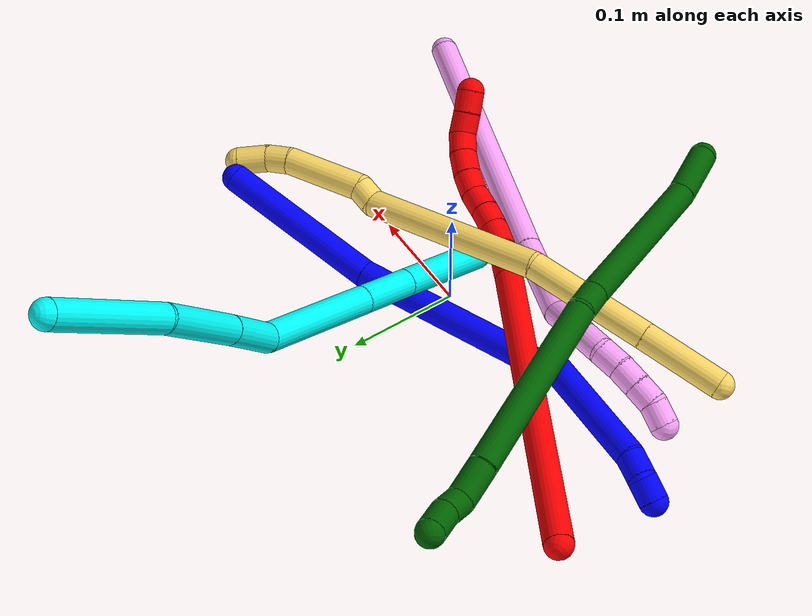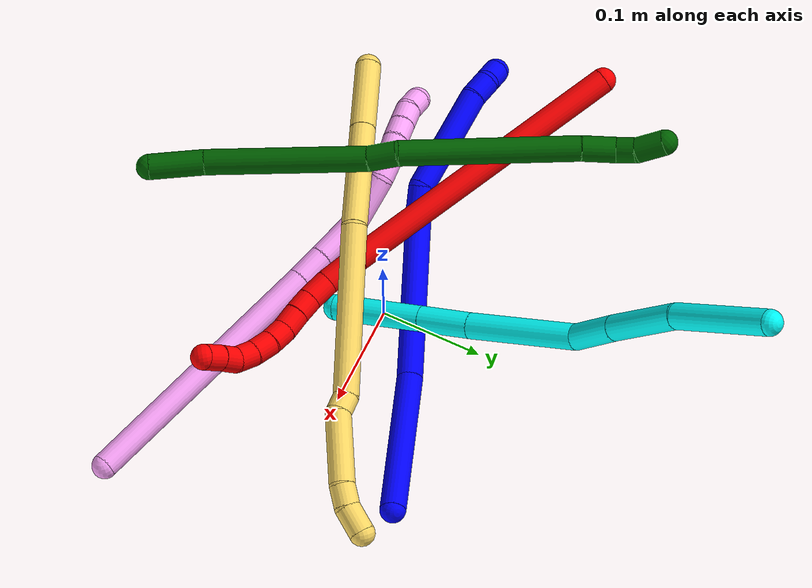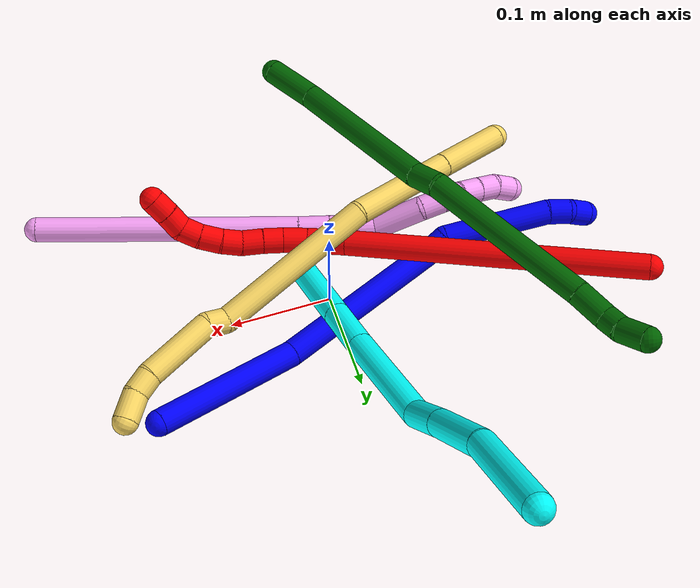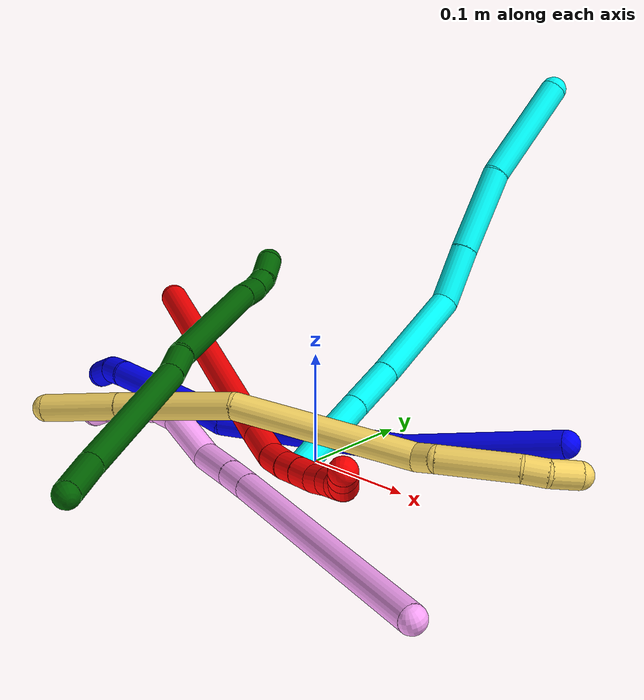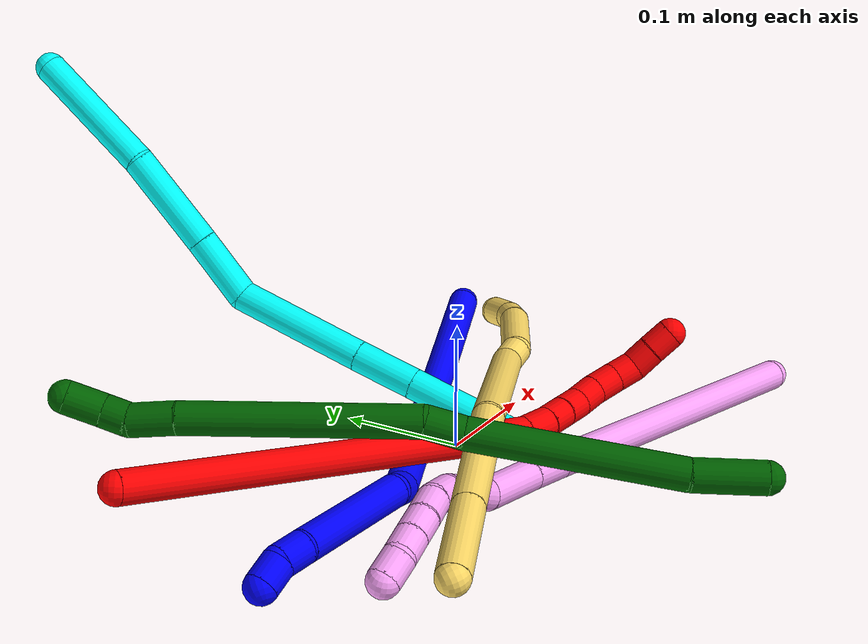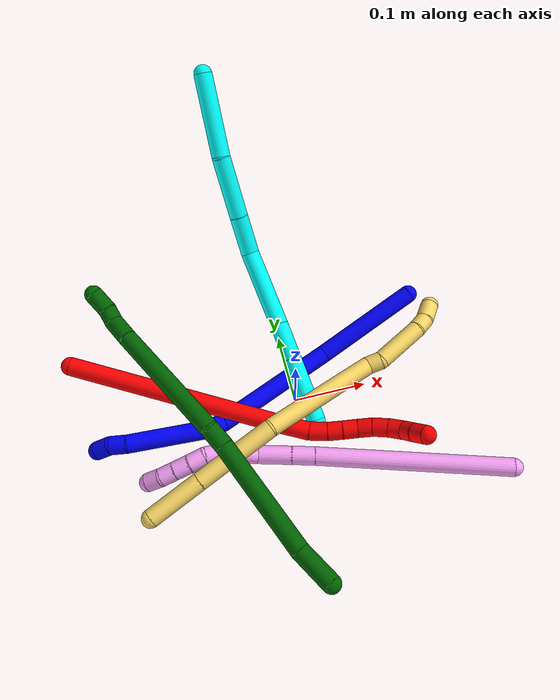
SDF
<sdf version="1.7">
 <world name="default">
  <plugin name="TubeGeneratorPlugin" filename="libtube_generator_plugin.so"/>
  <model name="photoneo_s_sensor">
   <static>1</static>
   <pose>0 0 2 1.57079 1.57079 3.14159</pose>
   <link name="link">
    <inertial><mass>0.1</mass></inertial>
    <sensor name="sensor" type="depth">
     <update_rate>30</update_rate>
     <camera>
      <horizontal_fov>1.22</horizontal_fov>
      <image><width>1920</width><height>1200</height><format>B8G8R8</format></image>
      <clip><near>0.1</near><far>4</far></clip>
      <depth_camera><output>points</output></depth_camera>
     </camera>
     <plugin name="camera_plugin" filename="libgazebo_ros_depth_camera.so">
      <baseline>0.2</baseline>
      <alwaysOn>1</alwaysOn>
      <updateRate>0.0</updateRate>
      <cameraName>camera_ir</cameraName>
      <imageTopicName>/camera/color/image_raw</imageTopicName>
      <cameraInfoTopicName>/camera/color/camera_info</cameraInfoTopicName>
      <depthImageTopicName>/camera/depth/image_raw</depthImageTopicName>
      <depthImageCameraInfoTopicName>/camera/depth/camera_info</depthImageCameraInfoTopicName>
      <pointCloudTopicName>/camera/depth/points</pointCloudTopicName>
      <frameName>fr_optical</frameName>
      <pointCloudCutoff>0.1</pointCloudCutoff>
      <pointCloudCutoffMax>2.0</pointCloudCutoffMax>
      <distortionK1>0</distortionK1>
      <distortionK2>0</distortionK2>
      <distortionK3>0</distortionK3>
      <distortionT1>0</distortionT1>
      <distortionT2>0</distortionT2>
      <CxPrime>0</CxPrime>
      <Cx>0</Cx>
      <Cy>0</Cy>
      <focalLength>0</focalLength>
      <hackBaseline>0</hackBaseline>
     </plugin>
    </sensor>
   </link>
  </model>
  <gravity>0 0 -9.8</gravity>
  <magnetic_field>6e-06 2.3e-05 -4.2e-05</magnetic_field>
  <atmosphere type="adiabatic"/>
  <physics name="default_physics" default="0" type="ode">
   <max_step_size>0.003</max_step_size>
   <real_time_factor>1</real_time_factor>
   <real_time_update_rate>1000</real_time_update_rate>
   <max_contacts>10000</max_contacts>
   <ode>
    <solver>
     <type>quick</type>
     <iters>100</iters>
     <sor>1.3</sor>
     <use_dynamic_moi_rescaling>0</use_dynamic_moi_rescaling>
    </solver>
    <constraints>
     <contact_max_correcting_vel>0</contact_max_correcting_vel>
     <contact_surface_layer>0.001</contact_surface_layer>
     <cfm>0</cfm>
     <erp>0.2</erp>
    </constraints>
   </ode>
  </physics>
  <scene><ambient>0.4 0.4 0.4 1</ambient><background>0.7 0.7 0.7 1</background><shadows>0</shadows></scene>
  <audio><device>default</device></audio>
  <spherical_coordinates>
   <surface_model>EARTH_WGS84</surface_model>
   <latitude_deg>0</latitude_deg>
   <longitude_deg>0</longitude_deg>
   <elevation>0</elevation>
   <heading_deg>0</heading_deg>
  </spherical_coordinates>
  <model name="bin">
   <static>1</static>
   <link name="bottom">
    <collision name="collision-bottom">
     <pose>0 0 -0.01 0 -0 0</pose>
     <geometry><box><size>0.8 0.6 0.02</size></box></geometry>
     <surface>
      <friction><ode><mu>100</mu><mu2>100</mu2></ode></friction>
      <contact><collide_bitmask>65535</collide_bitmask></contact>
     </surface>
    </collision>
   </link>
   <link name="west_wall">
    <collision name="collision-west_wall">
     <pose>-0.41 0 0.1 0 -0 0</pose>
     <geometry><box><size>0.02 0.6 0.2</size></box></geometry>
     <surface>
      <friction><ode><mu>100</mu><mu2>100</mu2></ode></friction>
      <contact><collide_bitmask>65535</collide_bitmask></contact>
     </surface>
    </collision>
   </link>
   <link name="east_wall">
    <collision name="collision-east_wall">
     <pose>0.41 0 0.1 0 -0 0</pose>
     <geometry><box><size>0.02 0.6 0.2</size></box></geometry>
     <surface>
      <friction><ode><mu>100</mu><mu2>100</mu2></ode></friction>
      <contact><collide_bitmask>65535</collide_bitmask></contact>
     </surface>
    </collision>
   </link>
   <link name="south_wall">
    <collision name="collision-south_wall">
     <pose>0 -0.31 0.1 0 -0 0</pose>
     <geometry><box><size>0.8 0.02 0.2</size></box></geometry>
     <surface>
      <friction><ode><mu>100</mu><mu2>100</mu2></ode></friction>
      <contact><collide_bitmask>65535</collide_bitmask></contact>
     </surface>
    </collision>
   </link>
   <link name="north_wall">
    <collision name="collision-north_wall">
     <pose>0 0.31 0.1 0 -0 0</pose>
     <geometry><box><size>0.8 0.02 0.2</size></box></geometry>
     <surface>
      <friction><ode><mu>100</mu><mu2>100</mu2></ode></friction>
      <contact><collide_bitmask>65535</collide_bitmask></contact>
     </surface>
    </collision>
   </link>
  </model>
  <model name="1">
   <static>0</static>
   <link name="1">
    <collision name="collision-cylinder-e_1_1_4">
     <pose>-0.056085 -0.009486 -0.048654 2.94903 -0.846986 -2.71946</pose>
     <geometry><cylinder><radius>0.0125</radius><length>0.149703</length></cylinder></geometry>
     <surface>
      <friction><ode><mu>1.16</mu><mu2>1.16</mu2><slip1>0</slip1><slip2>0</slip2></ode></friction>
      <contact><ode><kp>1e+06</kp><kd>1</kd><max_vel>0</max_vel><min_depth>0.001</min_depth></ode></contact>
     </surface>
    </collision>
    <visual name="visual-cylinder-e_1_1_4">
     <pose>-0.056085 -0.009486 -0.048654 2.94903 -0.846986 -2.71946</pose>
     <geometry><cylinder><radius>0.0125</radius><length>0.149703</length></cylinder></geometry>
     <material><ambient>0 0 1 1</ambient></material>
    </visual>
    <collision name="collision-cylinder-e_2_4_5">
     <pose>-0.18061 -0.045147 -0.144432 2.63459 -0.903636 -2.16087</pose>
     <geometry><cylinder><radius>0.0125</radius><length>0.174238</length></cylinder></geometry>
     <surface>
      <friction><ode><mu>1.16</mu><mu2>1.16</mu2><slip1>0</slip1><slip2>0</slip2></ode></friction>
      <contact><ode><kp>1e+06</kp><kd>1</kd><max_vel>0</max_vel><min_depth>0.001</min_depth></ode></contact>
     </surface>
    </collision>
    <visual name="visual-cylinder-e_2_4_5">
     <pose>-0.18061 -0.045147 -0.144432 2.63459 -0.903636 -2.16087</pose>
     <geometry><cylinder><radius>0.0125</radius><length>0.174238</length></cylinder></geometry>
     <material><ambient>0 0 1 1</ambient></material>
    </visual>
    <collision name="collision-cylinder-e_3_5_6">
     <pose>-0.25981 -0.077099 -0.194282 2.01166 -1.03507 -1.46352</pose>
     <geometry><cylinder><radius>0.0125</radius><length>0.02503</length></cylinder></geometry>
     <surface>
      <friction><ode><mu>1.16</mu><mu2>1.16</mu2><slip1>0</slip1><slip2>0</slip2></ode></friction>
      <contact><ode><kp>1e+06</kp><kd>1</kd><max_vel>0</max_vel><min_depth>0.001</min_depth></ode></contact>
     </surface>
    </collision>
    <visual name="visual-cylinder-e_3_5_6">
     <pose>-0.25981 -0.077099 -0.194282 2.01166 -1.03507 -1.46352</pose>
     <geometry><cylinder><radius>0.0125</radius><length>0.02503</length></cylinder></geometry>
     <material><ambient>0 0 1 1</ambient></material>
    </visual>
    <collision name="collision-cylinder-e_4_6_7">
     <pose>-0.322246 -0.082528 -0.212382 -3.11889 -1.28155 3.11115</pose>
     <geometry><cylinder><radius>0.0125</radius><length>0.107827</length></cylinder></geometry>
     <surface>
      <friction><ode><mu>1.16</mu><mu2>1.16</mu2><slip1>0</slip1><slip2>0</slip2></ode></friction>
      <contact><ode><kp>1e+06</kp><kd>1</kd><max_vel>0</max_vel><min_depth>0.001</min_depth></ode></contact>
     </surface>
    </collision>
    <visual name="visual-cylinder-e_4_6_7">
     <pose>-0.322246 -0.082528 -0.212382 -3.11889 -1.28155 3.11115</pose>
     <geometry><cylinder><radius>0.0125</radius><length>0.107827</length></cylinder></geometry>
     <material><ambient>0 0 1 1</ambient></material>
    </visual>
    <collision name="collision-cylinder-e_5_7_8">
     <pose>-0.384368 -0.079668 -0.231014 -2.48507 -1.19569 2.21407</pose>
     <geometry><cylinder><radius>0.0125</radius><length>0.022458</length></cylinder></geometry>
     <surface>
      <friction><ode><mu>1.16</mu><mu2>1.16</mu2><slip1>0</slip1><slip2>0</slip2></ode></friction>
      <contact><ode><kp>1e+06</kp><kd>1</kd><max_vel>0</max_vel><min_depth>0.001</min_depth></ode></contact>
     </surface>
    </collision>
    <visual name="visual-cylinder-e_5_7_8">
     <pose>-0.384368 -0.079668 -0.231014 -2.48507 -1.19569 2.21407</pose>
     <geometry><cylinder><radius>0.0125</radius><length>0.022458</length></cylinder></geometry>
     <material><ambient>0 0 1 1</ambient></material>
    </visual>
    <collision name="collision-cylinder-e_6_8_2">
     <pose>-0.402359 -0.073632 -0.240459 -2.62364 -0.814315 2.03984</pose>
     <geometry><cylinder><radius>0.0125</radius><length>0.020744</length></cylinder></geometry>
     <surface>
      <friction><ode><mu>1.16</mu><mu2>1.16</mu2><slip1>0</slip1><slip2>0</slip2></ode></friction>
      <contact><ode><kp>1e+06</kp><kd>1</kd><max_vel>0</max_vel><min_depth>0.001</min_depth></ode></contact>
     </surface>
    </collision>
    <visual name="visual-cylinder-e_6_8_2">
     <pose>-0.402359 -0.073632 -0.240459 -2.62364 -0.814315 2.03984</pose>
     <geometry><cylinder><radius>0.0125</radius><length>0.020744</length></cylinder></geometry>
     <material><ambient>0 0 1 1</ambient></material>
    </visual>
    <collision name="collision-sphere-2">
     <pose>-0.409903 -0.070107 -0.246644 0 -0 0</pose>
     <geometry><sphere><radius>0.0125</radius></sphere></geometry>
     <surface>
      <friction><ode><mu>1.16</mu><mu2>1.16</mu2><slip1>0</slip1><slip2>0</slip2></ode></friction>
      <contact><ode><kp>1e+06</kp><kd>1</kd><max_vel>0</max_vel><min_depth>0.001</min_depth></ode></contact>
     </surface>
    </collision>
    <visual name="visual-sphere-2">
     <pose>-0.409903 -0.070107 -0.246644 0 -0 0</pose>
     <geometry><sphere><radius>0.0125</radius></sphere></geometry>
     <material><ambient>0 0 1 1</ambient></material>
    </visual>
    <collision name="collision-sphere-4">
     <pose>-0.112171 -0.018973 -0.097308 0 -0 0</pose>
     <geometry><sphere><radius>0.0125</radius></sphere></geometry>
     <surface>
      <friction><ode><mu>1.16</mu><mu2>1.16</mu2><slip1>0</slip1><slip2>0</slip2></ode></friction>
      <contact><ode><kp>1e+06</kp><kd>1</kd><max_vel>0</max_vel><min_depth>0.001</min_depth></ode></contact>
     </surface>
    </collision>
    <visual name="visual-sphere-4">
     <pose>-0.112171 -0.018973 -0.097308 0 -0 0</pose>
     <geometry><sphere><radius>0.0125</radius></sphere></geometry>
     <material><ambient>0 0 1 1</ambient></material>
    </visual>
    <collision name="collision-sphere-1">
     <geometry><sphere><radius>0.0125</radius></sphere></geometry>
     <surface>
      <friction><ode><mu>1.16</mu><mu2>1.16</mu2><slip1>0</slip1><slip2>0</slip2></ode></friction>
      <contact><ode><kp>1e+06</kp><kd>1</kd><max_vel>0</max_vel><min_depth>0.001</min_depth></ode></contact>
     </surface>
    </collision>
    <visual name="visual-sphere-1">
     <geometry><sphere><radius>0.0125</radius></sphere></geometry>
     <material><ambient>0 0 1 1</ambient></material>
    </visual>
    <collision name="collision-sphere-8">
     <pose>-0.394816 -0.077157 -0.234273 0 -0 0</pose>
     <geometry><sphere><radius>0.0125</radius></sphere></geometry>
     <surface>
      <friction><ode><mu>1.16</mu><mu2>1.16</mu2><slip1>0</slip1><slip2>0</slip2></ode></friction>
      <contact><ode><kp>1e+06</kp><kd>1</kd><max_vel>0</max_vel><min_depth>0.001</min_depth></ode></contact>
     </surface>
    </collision>
    <visual name="visual-sphere-8">
     <pose>-0.394816 -0.077157 -0.234273 0 -0 0</pose>
     <geometry><sphere><radius>0.0125</radius></sphere></geometry>
     <material><ambient>0 0 1 1</ambient></material>
    </visual>
    <collision name="collision-sphere-5">
     <pose>-0.249049 -0.071322 -0.191556 0 -0 0</pose>
     <geometry><sphere><radius>0.0125</radius></sphere></geometry>
     <surface>
      <friction><ode><mu>1.16</mu><mu2>1.16</mu2><slip1>0</slip1><slip2>0</slip2></ode></friction>
      <contact><ode><kp>1e+06</kp><kd>1</kd><max_vel>0</max_vel><min_depth>0.001</min_depth></ode></contact>
     </surface>
    </collision>
    <visual name="visual-sphere-5">
     <pose>-0.249049 -0.071322 -0.191556 0 -0 0</pose>
     <geometry><sphere><radius>0.0125</radius></sphere></geometry>
     <material><ambient>0 0 1 1</ambient></material>
    </visual>
    <collision name="collision-sphere-6">
     <pose>-0.270572 -0.082877 -0.197008 0 -0 0</pose>
     <geometry><sphere><radius>0.0125</radius></sphere></geometry>
     <surface>
      <friction><ode><mu>1.16</mu><mu2>1.16</mu2><slip1>0</slip1><slip2>0</slip2></ode></friction>
      <contact><ode><kp>1e+06</kp><kd>1</kd><max_vel>0</max_vel><min_depth>0.001</min_depth></ode></contact>
     </surface>
    </collision>
    <visual name="visual-sphere-6">
     <pose>-0.270572 -0.082877 -0.197008 0 -0 0</pose>
     <geometry><sphere><radius>0.0125</radius></sphere></geometry>
     <material><ambient>0 0 1 1</ambient></material>
    </visual>
    <collision name="collision-sphere-7">
     <pose>-0.37392 -0.082179 -0.227756 0 -0 0</pose>
     <geometry><sphere><radius>0.0125</radius></sphere></geometry>
     <surface>
      <friction><ode><mu>1.16</mu><mu2>1.16</mu2><slip1>0</slip1><slip2>0</slip2></ode></friction>
      <contact><ode><kp>1e+06</kp><kd>1</kd><max_vel>0</max_vel><min_depth>0.001</min_depth></ode></contact>
     </surface>
    </collision>
    <visual name="visual-sphere-7">
     <pose>-0.37392 -0.082179 -0.227756 0 -0 0</pose>
     <geometry><sphere><radius>0.0125</radius></sphere></geometry>
     <material><ambient>0 0 1 1</ambient></material>
    </visual>
    <inertial>
     <pose>-0.196188 -0.046863 -0.140778 0 -0 0</pose>
     <mass>0.5</mass>
     <inertia>
      <ixx>-0.000697</ixx>
      <ixy>0</ixy>
      <ixz>0</ixz>
      <iyy>0.000433</iyy>
      <iyz>0</iyz>
      <izz>0.000825</izz>
     </inertia>
    </inertial>
   </link>
   <pose>0.193427 0.103572 0.041335 -0.719941 0.259501 -0.220732</pose>
  </model>
  <model name="2">
   <static>0</static>
   <link name="2">
    <collision name="collision-cylinder-e_1_1_4">
     <pose>0.065943 -0.015106 0.130286 0.115429 0.465862 0.027413</pose>
     <geometry><cylinder><radius>0.0125</radius><length>0.293605</length></cylinder></geometry>
     <surface>
      <friction><ode><mu>1.16</mu><mu2>1.16</mu2><slip1>0</slip1><slip2>0</slip2></ode></friction>
      <contact><ode><kp>1e+06</kp><kd>1</kd><max_vel>0</max_vel><min_depth>0.001</min_depth></ode></contact>
     </surface>
    </collision>
    <visual name="visual-cylinder-e_1_1_4">
     <pose>0.065943 -0.015106 0.130286 0.115429 0.465862 0.027413</pose>
     <geometry><cylinder><radius>0.0125</radius><length>0.293605</length></cylinder></geometry>
     <material><ambient>1 0 0 1</ambient></material>
    </visual>
    <collision name="collision-cylinder-e_2_4_5">
     <pose>0.141013 -0.032208 0.277366 0.118288 0.494882 0.029914</pose>
     <geometry><cylinder><radius>0.0125</radius><length>0.038438</length></cylinder></geometry>
     <surface>
      <friction><ode><mu>1.16</mu><mu2>1.16</mu2><slip1>0</slip1><slip2>0</slip2></ode></friction>
      <contact><ode><kp>1e+06</kp><kd>1</kd><max_vel>0</max_vel><min_depth>0.001</min_depth></ode></contact>
     </surface>
    </collision>
    <visual name="visual-cylinder-e_2_4_5">
     <pose>0.141013 -0.032208 0.277366 0.118288 0.494882 0.029914</pose>
     <geometry><cylinder><radius>0.0125</radius><length>0.038438</length></cylinder></geometry>
     <material><ambient>1 0 0 1</ambient></material>
    </visual>
    <collision name="collision-cylinder-e_3_5_6">
     <pose>0.157995 -0.033905 0.303803 -0.030921 0.683377 -0.010997</pose>
     <geometry><cylinder><radius>0.0125</radius><length>0.024879</length></cylinder></geometry>
     <surface>
      <friction><ode><mu>1.16</mu><mu2>1.16</mu2><slip1>0</slip1><slip2>0</slip2></ode></friction>
      <contact><ode><kp>1e+06</kp><kd>1</kd><max_vel>0</max_vel><min_depth>0.001</min_depth></ode></contact>
     </surface>
    </collision>
    <visual name="visual-cylinder-e_3_5_6">
     <pose>0.157995 -0.033905 0.303803 -0.030921 0.683377 -0.010997</pose>
     <geometry><cylinder><radius>0.0125</radius><length>0.024879</length></cylinder></geometry>
     <material><ambient>1 0 0 1</ambient></material>
    </visual>
    <collision name="collision-cylinder-e_4_6_7">
     <pose>0.172976 -0.032972 0.320445 -0.09043 0.792303 -0.037845</pose>
     <geometry><cylinder><radius>0.0125</radius><length>0.02002</length></cylinder></geometry>
     <surface>
      <friction><ode><mu>1.16</mu><mu2>1.16</mu2><slip1>0</slip1><slip2>0</slip2></ode></friction>
      <contact><ode><kp>1e+06</kp><kd>1</kd><max_vel>0</max_vel><min_depth>0.001</min_depth></ode></contact>
     </surface>
    </collision>
    <visual name="visual-cylinder-e_4_6_7">
     <pose>0.172976 -0.032972 0.320445 -0.09043 0.792303 -0.037845</pose>
     <geometry><cylinder><radius>0.0125</radius><length>0.02002</length></cylinder></geometry>
     <material><ambient>1 0 0 1</ambient></material>
    </visual>
    <collision name="collision-cylinder-e_5_7_8">
     <pose>0.187844 -0.032249 0.334522 -0.012589 0.83012 -0.005548</pose>
     <geometry><cylinder><radius>0.0125</radius><length>0.020976</length></cylinder></geometry>
     <surface>
      <friction><ode><mu>1.16</mu><mu2>1.16</mu2><slip1>0</slip1><slip2>0</slip2></ode></friction>
      <contact><ode><kp>1e+06</kp><kd>1</kd><max_vel>0</max_vel><min_depth>0.001</min_depth></ode></contact>
     </surface>
    </collision>
    <visual name="visual-cylinder-e_5_7_8">
     <pose>0.187844 -0.032249 0.334522 -0.012589 0.83012 -0.005548</pose>
     <geometry><cylinder><radius>0.0125</radius><length>0.020976</length></cylinder></geometry>
     <material><ambient>1 0 0 1</ambient></material>
    </visual>
    <collision name="collision-cylinder-e_6_8_9">
     <pose>0.202432 -0.029873 0.348865 -0.304823 0.732194 -0.11764</pose>
     <geometry><cylinder><radius>0.0125</radius><length>0.020486</length></cylinder></geometry>
     <surface>
      <friction><ode><mu>1.16</mu><mu2>1.16</mu2><slip1>0</slip1><slip2>0</slip2></ode></friction>
      <contact><ode><kp>1e+06</kp><kd>1</kd><max_vel>0</max_vel><min_depth>0.001</min_depth></ode></contact>
     </surface>
    </collision>
    <visual name="visual-cylinder-e_6_8_9">
     <pose>0.202432 -0.029873 0.348865 -0.304823 0.732194 -0.11764</pose>
     <geometry><cylinder><radius>0.0125</radius><length>0.020486</length></cylinder></geometry>
     <material><ambient>1 0 0 1</ambient></material>
    </visual>
    <collision name="collision-cylinder-e_7_9_10">
     <pose>0.215159 -0.024926 0.364732 -0.300005 0.578607 -0.089913</pose>
     <geometry><cylinder><radius>0.0125</radius><length>0.021506</length></cylinder></geometry>
     <surface>
      <friction><ode><mu>1.16</mu><mu2>1.16</mu2><slip1>0</slip1><slip2>0</slip2></ode></friction>
      <contact><ode><kp>1e+06</kp><kd>1</kd><max_vel>0</max_vel><min_depth>0.001</min_depth></ode></contact>
     </surface>
    </collision>
    <visual name="visual-cylinder-e_7_9_10">
     <pose>0.215159 -0.024926 0.364732 -0.300005 0.578607 -0.089913</pose>
     <geometry><cylinder><radius>0.0125</radius><length>0.021506</length></cylinder></geometry>
     <material><ambient>1 0 0 1</ambient></material>
    </visual>
    <collision name="collision-cylinder-e_8_10_11">
     <pose>0.225174 -0.018707 0.381732 -0.400823 0.4255 -0.087707</pose>
     <geometry><cylinder><radius>0.0125</radius><length>0.02003</length></cylinder></geometry>
     <surface>
      <friction><ode><mu>1.16</mu><mu2>1.16</mu2><slip1>0</slip1><slip2>0</slip2></ode></friction>
      <contact><ode><kp>1e+06</kp><kd>1</kd><max_vel>0</max_vel><min_depth>0.001</min_depth></ode></contact>
     </surface>
    </collision>
    <visual name="visual-cylinder-e_8_10_11">
     <pose>0.225174 -0.018707 0.381732 -0.400823 0.4255 -0.087707</pose>
     <geometry><cylinder><radius>0.0125</radius><length>0.02003</length></cylinder></geometry>
     <material><ambient>1 0 0 1</ambient></material>
    </visual>
    <collision name="collision-cylinder-e_9_11_12">
     <pose>0.230958 -0.007955 0.396891 -0.816406 0.165663 -0.071782</pose>
     <geometry><cylinder><radius>0.0125</radius><length>0.020016</length></cylinder></geometry>
     <surface>
      <friction><ode><mu>1.16</mu><mu2>1.16</mu2><slip1>0</slip1><slip2>0</slip2></ode></friction>
      <contact><ode><kp>1e+06</kp><kd>1</kd><max_vel>0</max_vel><min_depth>0.001</min_depth></ode></contact>
     </surface>
    </collision>
    <visual name="visual-cylinder-e_9_11_12">
     <pose>0.230958 -0.007955 0.396891 -0.816406 0.165663 -0.071782</pose>
     <geometry><cylinder><radius>0.0125</radius><length>0.020016</length></cylinder></geometry>
     <material><ambient>1 0 0 1</ambient></material>
    </visual>
    <collision name="collision-cylinder-e_10_12_2">
     <pose>0.234712 0.006002 0.410741 -0.7619 0.21144 -0.08495</pose>
     <geometry><cylinder><radius>0.0125</radius><length>0.020044</length></cylinder></geometry>
     <surface>
      <friction><ode><mu>1.16</mu><mu2>1.16</mu2><slip1>0</slip1><slip2>0</slip2></ode></friction>
      <contact><ode><kp>1e+06</kp><kd>1</kd><max_vel>0</max_vel><min_depth>0.001</min_depth></ode></contact>
     </surface>
    </collision>
    <visual name="visual-cylinder-e_10_12_2">
     <pose>0.234712 0.006002 0.410741 -0.7619 0.21144 -0.08495</pose>
     <geometry><cylinder><radius>0.0125</radius><length>0.020044</length></cylinder></geometry>
     <material><ambient>1 0 0 1</ambient></material>
    </visual>
    <collision name="collision-sphere-2">
     <pose>0.236815 0.012766 0.41783 0 -0 0</pose>
     <geometry><sphere><radius>0.0125</radius></sphere></geometry>
     <surface>
      <friction><ode><mu>1.16</mu><mu2>1.16</mu2><slip1>0</slip1><slip2>0</slip2></ode></friction>
      <contact><ode><kp>1e+06</kp><kd>1</kd><max_vel>0</max_vel><min_depth>0.001</min_depth></ode></contact>
     </surface>
    </collision>
    <visual name="visual-sphere-2">
     <pose>0.236815 0.012766 0.41783 0 -0 0</pose>
     <geometry><sphere><radius>0.0125</radius></sphere></geometry>
     <material><ambient>1 0 0 1</ambient></material>
    </visual>
    <collision name="collision-sphere-12">
     <pose>0.232608 -0.000762 0.403651 0 -0 0</pose>
     <geometry><sphere><radius>0.0125</radius></sphere></geometry>
     <surface>
      <friction><ode><mu>1.16</mu><mu2>1.16</mu2><slip1>0</slip1><slip2>0</slip2></ode></friction>
      <contact><ode><kp>1e+06</kp><kd>1</kd><max_vel>0</max_vel><min_depth>0.001</min_depth></ode></contact>
     </surface>
    </collision>
    <visual name="visual-sphere-12">
     <pose>0.232608 -0.000762 0.403651 0 -0 0</pose>
     <geometry><sphere><radius>0.0125</radius></sphere></geometry>
     <material><ambient>1 0 0 1</ambient></material>
    </visual>
    <collision name="collision-sphere-11">
     <pose>0.229308 -0.015147 0.390131 0 -0 0</pose>
     <geometry><sphere><radius>0.0125</radius></sphere></geometry>
     <surface>
      <friction><ode><mu>1.16</mu><mu2>1.16</mu2><slip1>0</slip1><slip2>0</slip2></ode></friction>
      <contact><ode><kp>1e+06</kp><kd>1</kd><max_vel>0</max_vel><min_depth>0.001</min_depth></ode></contact>
     </surface>
    </collision>
    <visual name="visual-sphere-11">
     <pose>0.229308 -0.015147 0.390131 0 -0 0</pose>
     <geometry><sphere><radius>0.0125</radius></sphere></geometry>
     <material><ambient>1 0 0 1</ambient></material>
    </visual>
    <collision name="collision-sphere-10">
     <pose>0.22104 -0.022266 0.373333 0 -0 0</pose>
     <geometry><sphere><radius>0.0125</radius></sphere></geometry>
     <surface>
      <friction><ode><mu>1.16</mu><mu2>1.16</mu2><slip1>0</slip1><slip2>0</slip2></ode></friction>
      <contact><ode><kp>1e+06</kp><kd>1</kd><max_vel>0</max_vel><min_depth>0.001</min_depth></ode></contact>
     </surface>
    </collision>
    <visual name="visual-sphere-10">
     <pose>0.22104 -0.022266 0.373333 0 -0 0</pose>
     <geometry><sphere><radius>0.0125</radius></sphere></geometry>
     <material><ambient>1 0 0 1</ambient></material>
    </visual>
    <collision name="collision-sphere-9">
     <pose>0.209279 -0.027587 0.356132 0 -0 0</pose>
     <geometry><sphere><radius>0.0125</radius></sphere></geometry>
     <surface>
      <friction><ode><mu>1.16</mu><mu2>1.16</mu2><slip1>0</slip1><slip2>0</slip2></ode></friction>
      <contact><ode><kp>1e+06</kp><kd>1</kd><max_vel>0</max_vel><min_depth>0.001</min_depth></ode></contact>
     </surface>
    </collision>
    <visual name="visual-sphere-9">
     <pose>0.209279 -0.027587 0.356132 0 -0 0</pose>
     <geometry><sphere><radius>0.0125</radius></sphere></geometry>
     <material><ambient>1 0 0 1</ambient></material>
    </visual>
    <collision name="collision-sphere-4">
     <pose>0.131885 -0.030212 0.260571 0 -0 0</pose>
     <geometry><sphere><radius>0.0125</radius></sphere></geometry>
     <surface>
      <friction><ode><mu>1.16</mu><mu2>1.16</mu2><slip1>0</slip1><slip2>0</slip2></ode></friction>
      <contact><ode><kp>1e+06</kp><kd>1</kd><max_vel>0</max_vel><min_depth>0.001</min_depth></ode></contact>
     </surface>
    </collision>
    <visual name="visual-sphere-4">
     <pose>0.131885 -0.030212 0.260571 0 -0 0</pose>
     <geometry><sphere><radius>0.0125</radius></sphere></geometry>
     <material><ambient>1 0 0 1</ambient></material>
    </visual>
    <collision name="collision-sphere-1">
     <geometry><sphere><radius>0.0125</radius></sphere></geometry>
     <surface>
      <friction><ode><mu>1.16</mu><mu2>1.16</mu2><slip1>0</slip1><slip2>0</slip2></ode></friction>
      <contact><ode><kp>1e+06</kp><kd>1</kd><max_vel>0</max_vel><min_depth>0.001</min_depth></ode></contact>
     </surface>
    </collision>
    <visual name="visual-sphere-1">
     <geometry><sphere><radius>0.0125</radius></sphere></geometry>
     <material><ambient>1 0 0 1</ambient></material>
    </visual>
    <collision name="collision-sphere-8">
     <pose>0.195584 -0.032159 0.341598 0 -0 0</pose>
     <geometry><sphere><radius>0.0125</radius></sphere></geometry>
     <surface>
      <friction><ode><mu>1.16</mu><mu2>1.16</mu2><slip1>0</slip1><slip2>0</slip2></ode></friction>
      <contact><ode><kp>1e+06</kp><kd>1</kd><max_vel>0</max_vel><min_depth>0.001</min_depth></ode></contact>
     </surface>
    </collision>
    <visual name="visual-sphere-8">
     <pose>0.195584 -0.032159 0.341598 0 -0 0</pose>
     <geometry><sphere><radius>0.0125</radius></sphere></geometry>
     <material><ambient>1 0 0 1</ambient></material>
    </visual>
    <collision name="collision-sphere-5">
     <pose>0.15014 -0.034204 0.294161 0 -0 0</pose>
     <geometry><sphere><radius>0.0125</radius></sphere></geometry>
     <surface>
      <friction><ode><mu>1.16</mu><mu2>1.16</mu2><slip1>0</slip1><slip2>0</slip2></ode></friction>
      <contact><ode><kp>1e+06</kp><kd>1</kd><max_vel>0</max_vel><min_depth>0.001</min_depth></ode></contact>
     </surface>
    </collision>
    <visual name="visual-sphere-5">
     <pose>0.15014 -0.034204 0.294161 0 -0 0</pose>
     <geometry><sphere><radius>0.0125</radius></sphere></geometry>
     <material><ambient>1 0 0 1</ambient></material>
    </visual>
    <collision name="collision-sphere-6">
     <pose>0.165849 -0.033607 0.313444 0 -0 0</pose>
     <geometry><sphere><radius>0.0125</radius></sphere></geometry>
     <surface>
      <friction><ode><mu>1.16</mu><mu2>1.16</mu2><slip1>0</slip1><slip2>0</slip2></ode></friction>
      <contact><ode><kp>1e+06</kp><kd>1</kd><max_vel>0</max_vel><min_depth>0.001</min_depth></ode></contact>
     </surface>
    </collision>
    <visual name="visual-sphere-6">
     <pose>0.165849 -0.033607 0.313444 0 -0 0</pose>
     <geometry><sphere><radius>0.0125</radius></sphere></geometry>
     <material><ambient>1 0 0 1</ambient></material>
    </visual>
    <collision name="collision-sphere-7">
     <pose>0.180103 -0.032338 0.327445 0 -0 0</pose>
     <geometry><sphere><radius>0.0125</radius></sphere></geometry>
     <surface>
      <friction><ode><mu>1.16</mu><mu2>1.16</mu2><slip1>0</slip1><slip2>0</slip2></ode></friction>
      <contact><ode><kp>1e+06</kp><kd>1</kd><max_vel>0</max_vel><min_depth>0.001</min_depth></ode></contact>
     </surface>
    </collision>
    <visual name="visual-sphere-7">
     <pose>0.180103 -0.032338 0.327445 0 -0 0</pose>
     <geometry><sphere><radius>0.0125</radius></sphere></geometry>
     <material><ambient>1 0 0 1</ambient></material>
    </visual>
    <inertial>
     <pose>0.117454 -0.01883 0.217437 0 -0 0</pose>
     <mass>0.5</mass>
     <inertia>
      <ixx>0.00198</ixx>
      <ixy>0</ixy>
      <ixz>0</ixz>
      <iyy>0.002179</iyy>
      <iyz>0</iyz>
      <izz>-0.000714</izz>
     </inertia>
    </inertial>
   </link>
   <pose>-0.287962 0.095423 0.061016 1.649 -0.127595 0.593899</pose>
  </model>
  <model name="3">
   <static>0</static>
   <link name="3">
    <collision name="collision-cylinder-e_1_1_4">
     <pose>0.001665 0.000396 -0.055247 -3.13443 0.030123 -2.67467</pose>
     <geometry><cylinder><radius>0.0125</radius><length>0.110547</length></cylinder></geometry>
     <surface>
      <friction><ode><mu>1.16</mu><mu2>1.16</mu2><slip1>0</slip1><slip2>0</slip2></ode></friction>
      <contact><ode><kp>1e+06</kp><kd>1</kd><max_vel>0</max_vel><min_depth>0.001</min_depth></ode></contact>
     </surface>
    </collision>
    <visual name="visual-cylinder-e_1_1_4">
     <pose>0.001665 0.000396 -0.055247 -3.13443 0.030123 -2.67467</pose>
     <geometry><cylinder><radius>0.0125</radius><length>0.110547</length></cylinder></geometry>
     <material><ambient>0.003922 1 0.996078 1</ambient></material>
    </visual>
    <collision name="collision-cylinder-e_2_4_5">
     <pose>0.008964 0.008596 -0.151176 -2.95205 0.135192 -1.23772</pose>
     <geometry><cylinder><radius>0.0125</radius><length>0.083611</length></cylinder></geometry>
     <surface>
      <friction><ode><mu>1.16</mu><mu2>1.16</mu2><slip1>0</slip1><slip2>0</slip2></ode></friction>
      <contact><ode><kp>1e+06</kp><kd>1</kd><max_vel>0</max_vel><min_depth>0.001</min_depth></ode></contact>
     </surface>
    </collision>
    <visual name="visual-cylinder-e_2_4_5">
     <pose>0.008964 0.008596 -0.151176 -2.95205 0.135192 -1.23772</pose>
     <geometry><cylinder><radius>0.0125</radius><length>0.083611</length></cylinder></geometry>
     <material><ambient>0.003922 1 0.996078 1</ambient></material>
    </visual>
    <collision name="collision-cylinder-e_3_5_6">
     <pose>0.018711 0.022517 -0.218588 -2.91666 0.148882 -1.16719</pose>
     <geometry><cylinder><radius>0.0125</radius><length>0.055454</length></cylinder></geometry>
     <surface>
      <friction><ode><mu>1.16</mu><mu2>1.16</mu2><slip1>0</slip1><slip2>0</slip2></ode></friction>
      <contact><ode><kp>1e+06</kp><kd>1</kd><max_vel>0</max_vel><min_depth>0.001</min_depth></ode></contact>
     </surface>
    </collision>
    <visual name="visual-cylinder-e_3_5_6">
     <pose>0.018711 0.022517 -0.218588 -2.91666 0.148882 -1.16719</pose>
     <geometry><cylinder><radius>0.0125</radius><length>0.055454</length></cylinder></geometry>
     <material><ambient>0.003922 1 0.996078 1</ambient></material>
    </visual>
    <collision name="collision-cylinder-e_4_6_7">
     <pose>0.030975 0.012667 -0.297021 2.84208 0.149495 0.921393</pose>
     <geometry><cylinder><radius>0.0125</radius><length>0.109447</length></cylinder></geometry>
     <surface>
      <friction><ode><mu>1.16</mu><mu2>1.16</mu2><slip1>0</slip1><slip2>0</slip2></ode></friction>
      <contact><ode><kp>1e+06</kp><kd>1</kd><max_vel>0</max_vel><min_depth>0.001</min_depth></ode></contact>
     </surface>
    </collision>
    <visual name="visual-cylinder-e_4_6_7">
     <pose>0.030975 0.012667 -0.297021 2.84208 0.149495 0.921393</pose>
     <geometry><cylinder><radius>0.0125</radius><length>0.109447</length></cylinder></geometry>
     <material><ambient>0.003922 1 0.996078 1</ambient></material>
    </visual>
    <collision name="collision-cylinder-e_5_7_8">
     <pose>0.042399 -0.011345 -0.372587 2.8164 0.129298 0.751759</pose>
     <geometry><cylinder><radius>0.0125</radius><length>0.050786</length></cylinder></geometry>
     <surface>
      <friction><ode><mu>1.16</mu><mu2>1.16</mu2><slip1>0</slip1><slip2>0</slip2></ode></friction>
      <contact><ode><kp>1e+06</kp><kd>1</kd><max_vel>0</max_vel><min_depth>0.001</min_depth></ode></contact>
     </surface>
    </collision>
    <visual name="visual-cylinder-e_5_7_8">
     <pose>0.042399 -0.011345 -0.372587 2.8164 0.129298 0.751759</pose>
     <geometry><cylinder><radius>0.0125</radius><length>0.050786</length></cylinder></geometry>
     <material><ambient>0.003922 1 0.996078 1</ambient></material>
    </visual>
    <collision name="collision-cylinder-e_6_8_2">
     <pose>0.051574 -0.033429 -0.438875 2.82203 0.131274 0.774561</pose>
     <geometry><cylinder><radius>0.0125</radius><length>0.090155</length></cylinder></geometry>
     <surface>
      <friction><ode><mu>1.16</mu><mu2>1.16</mu2><slip1>0</slip1><slip2>0</slip2></ode></friction>
      <contact><ode><kp>1e+06</kp><kd>1</kd><max_vel>0</max_vel><min_depth>0.001</min_depth></ode></contact>
     </surface>
    </collision>
    <visual name="visual-cylinder-e_6_8_2">
     <pose>0.051574 -0.033429 -0.438875 2.82203 0.131274 0.774561</pose>
     <geometry><cylinder><radius>0.0125</radius><length>0.090155</length></cylinder></geometry>
     <material><ambient>0.003922 1 0.996078 1</ambient></material>
    </visual>
    <collision name="collision-sphere-2">
     <pose>0.057474 -0.047468 -0.481302 0 -0 0</pose>
     <geometry><sphere><radius>0.0125</radius></sphere></geometry>
     <surface>
      <friction><ode><mu>1.16</mu><mu2>1.16</mu2><slip1>0</slip1><slip2>0</slip2></ode></friction>
      <contact><ode><kp>1e+06</kp><kd>1</kd><max_vel>0</max_vel><min_depth>0.001</min_depth></ode></contact>
     </surface>
    </collision>
    <visual name="visual-sphere-2">
     <pose>0.057474 -0.047468 -0.481302 0 -0 0</pose>
     <geometry><sphere><radius>0.0125</radius></sphere></geometry>
     <material><ambient>0.003922 1 0.996078 1</ambient></material>
    </visual>
    <collision name="collision-sphere-4">
     <pose>0.00333 0.000792 -0.110494 0 -0 0</pose>
     <geometry><sphere><radius>0.0125</radius></sphere></geometry>
     <surface>
      <friction><ode><mu>1.16</mu><mu2>1.16</mu2><slip1>0</slip1><slip2>0</slip2></ode></friction>
      <contact><ode><kp>1e+06</kp><kd>1</kd><max_vel>0</max_vel><min_depth>0.001</min_depth></ode></contact>
     </surface>
    </collision>
    <visual name="visual-sphere-4">
     <pose>0.00333 0.000792 -0.110494 0 -0 0</pose>
     <geometry><sphere><radius>0.0125</radius></sphere></geometry>
     <material><ambient>0.003922 1 0.996078 1</ambient></material>
    </visual>
    <collision name="collision-sphere-1">
     <geometry><sphere><radius>0.0125</radius></sphere></geometry>
     <surface>
      <friction><ode><mu>1.16</mu><mu2>1.16</mu2><slip1>0</slip1><slip2>0</slip2></ode></friction>
      <contact><ode><kp>1e+06</kp><kd>1</kd><max_vel>0</max_vel><min_depth>0.001</min_depth></ode></contact>
     </surface>
    </collision>
    <visual name="visual-sphere-1">
     <geometry><sphere><radius>0.0125</radius></sphere></geometry>
     <material><ambient>0.003922 1 0.996078 1</ambient></material>
    </visual>
    <collision name="collision-sphere-8">
     <pose>0.045673 -0.01939 -0.396448 0 -0 0</pose>
     <geometry><sphere><radius>0.0125</radius></sphere></geometry>
     <surface>
      <friction><ode><mu>1.16</mu><mu2>1.16</mu2><slip1>0</slip1><slip2>0</slip2></ode></friction>
      <contact><ode><kp>1e+06</kp><kd>1</kd><max_vel>0</max_vel><min_depth>0.001</min_depth></ode></contact>
     </surface>
    </collision>
    <visual name="visual-sphere-8">
     <pose>0.045673 -0.01939 -0.396448 0 -0 0</pose>
     <geometry><sphere><radius>0.0125</radius></sphere></geometry>
     <material><ambient>0.003922 1 0.996078 1</ambient></material>
    </visual>
    <collision name="collision-sphere-5">
     <pose>0.014599 0.016401 -0.191858 0 -0 0</pose>
     <geometry><sphere><radius>0.0125</radius></sphere></geometry>
     <surface>
      <friction><ode><mu>1.16</mu><mu2>1.16</mu2><slip1>0</slip1><slip2>0</slip2></ode></friction>
      <contact><ode><kp>1e+06</kp><kd>1</kd><max_vel>0</max_vel><min_depth>0.001</min_depth></ode></contact>
     </surface>
    </collision>
    <visual name="visual-sphere-5">
     <pose>0.014599 0.016401 -0.191858 0 -0 0</pose>
     <geometry><sphere><radius>0.0125</radius></sphere></geometry>
     <material><ambient>0.003922 1 0.996078 1</ambient></material>
    </visual>
    <collision name="collision-sphere-6">
     <pose>0.022824 0.028633 -0.245317 0 -0 0</pose>
     <geometry><sphere><radius>0.0125</radius></sphere></geometry>
     <surface>
      <friction><ode><mu>1.16</mu><mu2>1.16</mu2><slip1>0</slip1><slip2>0</slip2></ode></friction>
      <contact><ode><kp>1e+06</kp><kd>1</kd><max_vel>0</max_vel><min_depth>0.001</min_depth></ode></contact>
     </surface>
    </collision>
    <visual name="visual-sphere-6">
     <pose>0.022824 0.028633 -0.245317 0 -0 0</pose>
     <geometry><sphere><radius>0.0125</radius></sphere></geometry>
     <material><ambient>0.003922 1 0.996078 1</ambient></material>
    </visual>
    <collision name="collision-sphere-7">
     <pose>0.039125 -0.0033 -0.348725 0 -0 0</pose>
     <geometry><sphere><radius>0.0125</radius></sphere></geometry>
     <surface>
      <friction><ode><mu>1.16</mu><mu2>1.16</mu2><slip1>0</slip1><slip2>0</slip2></ode></friction>
      <contact><ode><kp>1e+06</kp><kd>1</kd><max_vel>0</max_vel><min_depth>0.001</min_depth></ode></contact>
     </surface>
    </collision>
    <visual name="visual-sphere-7">
     <pose>0.039125 -0.0033 -0.348725 0 -0 0</pose>
     <geometry><sphere><radius>0.0125</radius></sphere></geometry>
     <material><ambient>0.003922 1 0.996078 1</ambient></material>
    </visual>
    <inertial>
     <pose>0.024328 -0.000385 -0.243732 0 -0 0</pose>
     <mass>0.5</mass>
     <inertia><ixx>7.3e-05</ixx><ixy>0</ixy><ixz>0</ixz><iyy>-6e-06</iyy><iyz>0</iyz><izz>-3.4e-05</izz></inertia>
    </inertial>
   </link>
   <pose>-0.033489 0.369512 0.268136 -0.921437 0.070542 0.031692</pose>
  </model>
  <model name="4">
   <static>0</static>
   <link name="4">
    <collision name="collision-cylinder-e_1_1_4">
     <pose>-0.129312 0.028357 0.001191 -1.52883 -1.35473 1.31392</pose>
     <geometry><cylinder><radius>0.0125</radius><length>0.26478</length></cylinder></geometry>
     <surface>
      <friction><ode><mu>1.16</mu><mu2>1.16</mu2><slip1>0</slip1><slip2>0</slip2></ode></friction>
      <contact><ode><kp>1e+06</kp><kd>1</kd><max_vel>0</max_vel><min_depth>0.001</min_depth></ode></contact>
     </surface>
    </collision>
    <visual name="visual-cylinder-e_1_1_4">
     <pose>-0.129312 0.028357 0.001191 -1.52883 -1.35473 1.31392</pose>
     <geometry><cylinder><radius>0.0125</radius><length>0.26478</length></cylinder></geometry>
     <material><ambient>1 0.65098 0.996078 1</ambient></material>
    </visual>
    <collision name="collision-cylinder-e_2_4_5">
     <pose>-0.273725 0.060419 0.002257 -1.60443 -1.33014 1.36294</pose>
     <geometry><cylinder><radius>0.0125</radius><length>0.031099</length></cylinder></geometry>
     <surface>
      <friction><ode><mu>1.16</mu><mu2>1.16</mu2><slip1>0</slip1><slip2>0</slip2></ode></friction>
      <contact><ode><kp>1e+06</kp><kd>1</kd><max_vel>0</max_vel><min_depth>0.001</min_depth></ode></contact>
     </surface>
    </collision>
    <visual name="visual-cylinder-e_2_4_5">
     <pose>-0.273725 0.060419 0.002257 -1.60443 -1.33014 1.36294</pose>
     <geometry><cylinder><radius>0.0125</radius><length>0.031099</length></cylinder></geometry>
     <material><ambient>1 0.65098 0.996078 1</ambient></material>
    </visual>
    <collision name="collision-cylinder-e_3_5_6">
     <pose>-0.311508 0.069875 0.002469 -1.51244 -1.32202 1.26587</pose>
     <geometry><cylinder><radius>0.0125</radius><length>0.046803</length></cylinder></geometry>
     <surface>
      <friction><ode><mu>1.16</mu><mu2>1.16</mu2><slip1>0</slip1><slip2>0</slip2></ode></friction>
      <contact><ode><kp>1e+06</kp><kd>1</kd><max_vel>0</max_vel><min_depth>0.001</min_depth></ode></contact>
     </surface>
    </collision>
    <visual name="visual-cylinder-e_3_5_6">
     <pose>-0.311508 0.069875 0.002469 -1.51244 -1.32202 1.26587</pose>
     <geometry><cylinder><radius>0.0125</radius><length>0.046803</length></cylinder></geometry>
     <material><ambient>1 0.65098 0.996078 1</ambient></material>
    </visual>
    <collision name="collision-cylinder-e_4_6_7">
     <pose>-0.356661 0.081131 -0.008137 -2.67557 -1.07178 2.38121</pose>
     <geometry><cylinder><radius>0.0125</radius><length>0.051187</length></cylinder></geometry>
     <surface>
      <friction><ode><mu>1.16</mu><mu2>1.16</mu2><slip1>0</slip1><slip2>0</slip2></ode></friction>
      <contact><ode><kp>1e+06</kp><kd>1</kd><max_vel>0</max_vel><min_depth>0.001</min_depth></ode></contact>
     </surface>
    </collision>
    <visual name="visual-cylinder-e_4_6_7">
     <pose>-0.356661 0.081131 -0.008137 -2.67557 -1.07178 2.38121</pose>
     <geometry><cylinder><radius>0.0125</radius><length>0.051187</length></cylinder></geometry>
     <material><ambient>1 0.65098 0.996078 1</ambient></material>
    </visual>
    <collision name="collision-cylinder-e_5_7_8">
     <pose>-0.388567 0.091933 -0.021413 -1.9856 -1.02034 1.41807</pose>
     <geometry><cylinder><radius>0.0125</radius><length>0.022136</length></cylinder></geometry>
     <surface>
      <friction><ode><mu>1.16</mu><mu2>1.16</mu2><slip1>0</slip1><slip2>0</slip2></ode></friction>
      <contact><ode><kp>1e+06</kp><kd>1</kd><max_vel>0</max_vel><min_depth>0.001</min_depth></ode></contact>
     </surface>
    </collision>
    <visual name="visual-cylinder-e_5_7_8">
     <pose>-0.388567 0.091933 -0.021413 -1.9856 -1.02034 1.41807</pose>
     <geometry><cylinder><radius>0.0125</radius><length>0.022136</length></cylinder></geometry>
     <material><ambient>1 0.65098 0.996078 1</ambient></material>
    </visual>
    <collision name="collision-cylinder-e_6_8_9">
     <pose>-0.406127 0.104699 -0.023736 -1.56943 -0.827636 0.826629</pose>
     <geometry><cylinder><radius>0.0125</radius><length>0.022074</length></cylinder></geometry>
     <surface>
      <friction><ode><mu>1.16</mu><mu2>1.16</mu2><slip1>0</slip1><slip2>0</slip2></ode></friction>
      <contact><ode><kp>1e+06</kp><kd>1</kd><max_vel>0</max_vel><min_depth>0.001</min_depth></ode></contact>
     </surface>
    </collision>
    <visual name="visual-cylinder-e_6_8_9">
     <pose>-0.406127 0.104699 -0.023736 -1.56943 -0.827636 0.826629</pose>
     <geometry><cylinder><radius>0.0125</radius><length>0.022074</length></cylinder></geometry>
     <material><ambient>1 0.65098 0.996078 1</ambient></material>
    </visual>
    <collision name="collision-cylinder-e_7_9_10">
     <pose>-0.422238 0.118926 -0.022634 -1.4107 -0.861898 0.746284</pose>
     <geometry><cylinder><radius>0.0125</radius><length>0.021034</length></cylinder></geometry>
     <surface>
      <friction><ode><mu>1.16</mu><mu2>1.16</mu2><slip1>0</slip1><slip2>0</slip2></ode></friction>
      <contact><ode><kp>1e+06</kp><kd>1</kd><max_vel>0</max_vel><min_depth>0.001</min_depth></ode></contact>
     </surface>
    </collision>
    <visual name="visual-cylinder-e_7_9_10">
     <pose>-0.422238 0.118926 -0.022634 -1.4107 -0.861898 0.746284</pose>
     <geometry><cylinder><radius>0.0125</radius><length>0.021034</length></cylinder></geometry>
     <material><ambient>1 0.65098 0.996078 1</ambient></material>
    </visual>
    <collision name="collision-cylinder-e_8_10_11">
     <pose>-0.4378 0.132133 -0.020199 -1.36539 -0.855318 0.709844</pose>
     <geometry><cylinder><radius>0.0125</radius><length>0.020081</length></cylinder></geometry>
     <surface>
      <friction><ode><mu>1.16</mu><mu2>1.16</mu2><slip1>0</slip1><slip2>0</slip2></ode></friction>
      <contact><ode><kp>1e+06</kp><kd>1</kd><max_vel>0</max_vel><min_depth>0.001</min_depth></ode></contact>
     </surface>
    </collision>
    <visual name="visual-cylinder-e_8_10_11">
     <pose>-0.4378 0.132133 -0.020199 -1.36539 -0.855318 0.709844</pose>
     <geometry><cylinder><radius>0.0125</radius><length>0.020081</length></cylinder></geometry>
     <material><ambient>1 0.65098 0.996078 1</ambient></material>
    </visual>
    <collision name="collision-cylinder-e_9_11_2">
     <pose>-0.453259 0.143935 -0.01468 -0.90841 -0.859656 0.440384</pose>
     <geometry><cylinder><radius>0.0125</radius><length>0.020804</length></cylinder></geometry>
     <surface>
      <friction><ode><mu>1.16</mu><mu2>1.16</mu2><slip1>0</slip1><slip2>0</slip2></ode></friction>
      <contact><ode><kp>1e+06</kp><kd>1</kd><max_vel>0</max_vel><min_depth>0.001</min_depth></ode></contact>
     </surface>
    </collision>
    <visual name="visual-cylinder-e_9_11_2">
     <pose>-0.453259 0.143935 -0.01468 -0.90841 -0.859656 0.440384</pose>
     <geometry><cylinder><radius>0.0125</radius><length>0.020804</length></cylinder></geometry>
     <material><ambient>1 0.65098 0.996078 1</ambient></material>
    </visual>
    <collision name="collision-sphere-2">
     <pose>-0.46114 0.149289 -0.010505 0 -0 0</pose>
     <geometry><sphere><radius>0.0125</radius></sphere></geometry>
     <surface>
      <friction><ode><mu>1.16</mu><mu2>1.16</mu2><slip1>0</slip1><slip2>0</slip2></ode></friction>
      <contact><ode><kp>1e+06</kp><kd>1</kd><max_vel>0</max_vel><min_depth>0.001</min_depth></ode></contact>
     </surface>
    </collision>
    <visual name="visual-sphere-2">
     <pose>-0.46114 0.149289 -0.010505 0 -0 0</pose>
     <geometry><sphere><radius>0.0125</radius></sphere></geometry>
     <material><ambient>1 0.65098 0.996078 1</ambient></material>
    </visual>
    <collision name="collision-sphere-11">
     <pose>-0.445378 0.138581 -0.018856 0 -0 0</pose>
     <geometry><sphere><radius>0.0125</radius></sphere></geometry>
     <surface>
      <friction><ode><mu>1.16</mu><mu2>1.16</mu2><slip1>0</slip1><slip2>0</slip2></ode></friction>
      <contact><ode><kp>1e+06</kp><kd>1</kd><max_vel>0</max_vel><min_depth>0.001</min_depth></ode></contact>
     </surface>
    </collision>
    <visual name="visual-sphere-11">
     <pose>-0.445378 0.138581 -0.018856 0 -0 0</pose>
     <geometry><sphere><radius>0.0125</radius></sphere></geometry>
     <material><ambient>1 0.65098 0.996078 1</ambient></material>
    </visual>
    <collision name="collision-sphere-10">
     <pose>-0.430221 0.125685 -0.021542 0 -0 0</pose>
     <geometry><sphere><radius>0.0125</radius></sphere></geometry>
     <surface>
      <friction><ode><mu>1.16</mu><mu2>1.16</mu2><slip1>0</slip1><slip2>0</slip2></ode></friction>
      <contact><ode><kp>1e+06</kp><kd>1</kd><max_vel>0</max_vel><min_depth>0.001</min_depth></ode></contact>
     </surface>
    </collision>
    <visual name="visual-sphere-10">
     <pose>-0.430221 0.125685 -0.021542 0 -0 0</pose>
     <geometry><sphere><radius>0.0125</radius></sphere></geometry>
     <material><ambient>1 0.65098 0.996078 1</ambient></material>
    </visual>
    <collision name="collision-sphere-9">
     <pose>-0.414254 0.112167 -0.023725 0 -0 0</pose>
     <geometry><sphere><radius>0.0125</radius></sphere></geometry>
     <surface>
      <friction><ode><mu>1.16</mu><mu2>1.16</mu2><slip1>0</slip1><slip2>0</slip2></ode></friction>
      <contact><ode><kp>1e+06</kp><kd>1</kd><max_vel>0</max_vel><min_depth>0.001</min_depth></ode></contact>
     </surface>
    </collision>
    <visual name="visual-sphere-9">
     <pose>-0.414254 0.112167 -0.023725 0 -0 0</pose>
     <geometry><sphere><radius>0.0125</radius></sphere></geometry>
     <material><ambient>1 0.65098 0.996078 1</ambient></material>
    </visual>
    <collision name="collision-sphere-4">
     <pose>-0.258623 0.056715 0.002382 0 -0 0</pose>
     <geometry><sphere><radius>0.0125</radius></sphere></geometry>
     <surface>
      <friction><ode><mu>1.16</mu><mu2>1.16</mu2><slip1>0</slip1><slip2>0</slip2></ode></friction>
      <contact><ode><kp>1e+06</kp><kd>1</kd><max_vel>0</max_vel><min_depth>0.001</min_depth></ode></contact>
     </surface>
    </collision>
    <visual name="visual-sphere-4">
     <pose>-0.258623 0.056715 0.002382 0 -0 0</pose>
     <geometry><sphere><radius>0.0125</radius></sphere></geometry>
     <material><ambient>1 0.65098 0.996078 1</ambient></material>
    </visual>
    <collision name="collision-sphere-1">
     <geometry><sphere><radius>0.0125</radius></sphere></geometry>
     <surface>
      <friction><ode><mu>1.16</mu><mu2>1.16</mu2><slip1>0</slip1><slip2>0</slip2></ode></friction>
      <contact><ode><kp>1e+06</kp><kd>1</kd><max_vel>0</max_vel><min_depth>0.001</min_depth></ode></contact>
     </surface>
    </collision>
    <visual name="visual-sphere-1">
     <geometry><sphere><radius>0.0125</radius></sphere></geometry>
     <material><ambient>1 0.65098 0.996078 1</ambient></material>
    </visual>
    <collision name="collision-sphere-8">
     <pose>-0.398 0.097231 -0.023746 0 -0 0</pose>
     <geometry><sphere><radius>0.0125</radius></sphere></geometry>
     <surface>
      <friction><ode><mu>1.16</mu><mu2>1.16</mu2><slip1>0</slip1><slip2>0</slip2></ode></friction>
      <contact><ode><kp>1e+06</kp><kd>1</kd><max_vel>0</max_vel><min_depth>0.001</min_depth></ode></contact>
     </surface>
    </collision>
    <visual name="visual-sphere-8">
     <pose>-0.398 0.097231 -0.023746 0 -0 0</pose>
     <geometry><sphere><radius>0.0125</radius></sphere></geometry>
     <material><ambient>1 0.65098 0.996078 1</ambient></material>
    </visual>
    <collision name="collision-sphere-5">
     <pose>-0.288827 0.064123 0.002132 0 -0 0</pose>
     <geometry><sphere><radius>0.0125</radius></sphere></geometry>
     <surface>
      <friction><ode><mu>1.16</mu><mu2>1.16</mu2><slip1>0</slip1><slip2>0</slip2></ode></friction>
      <contact><ode><kp>1e+06</kp><kd>1</kd><max_vel>0</max_vel><min_depth>0.001</min_depth></ode></contact>
     </surface>
    </collision>
    <visual name="visual-sphere-5">
     <pose>-0.288827 0.064123 0.002132 0 -0 0</pose>
     <geometry><sphere><radius>0.0125</radius></sphere></geometry>
     <material><ambient>1 0.65098 0.996078 1</ambient></material>
    </visual>
    <collision name="collision-sphere-6">
     <pose>-0.334189 0.075627 0.002805 0 -0 0</pose>
     <geometry><sphere><radius>0.0125</radius></sphere></geometry>
     <surface>
      <friction><ode><mu>1.16</mu><mu2>1.16</mu2><slip1>0</slip1><slip2>0</slip2></ode></friction>
      <contact><ode><kp>1e+06</kp><kd>1</kd><max_vel>0</max_vel><min_depth>0.001</min_depth></ode></contact>
     </surface>
    </collision>
    <visual name="visual-sphere-6">
     <pose>-0.334189 0.075627 0.002805 0 -0 0</pose>
     <geometry><sphere><radius>0.0125</radius></sphere></geometry>
     <material><ambient>1 0.65098 0.996078 1</ambient></material>
    </visual>
    <collision name="collision-sphere-7">
     <pose>-0.379134 0.086634 -0.019079 0 -0 0</pose>
     <geometry><sphere><radius>0.0125</radius></sphere></geometry>
     <surface>
      <friction><ode><mu>1.16</mu><mu2>1.16</mu2><slip1>0</slip1><slip2>0</slip2></ode></friction>
      <contact><ode><kp>1e+06</kp><kd>1</kd><max_vel>0</max_vel><min_depth>0.001</min_depth></ode></contact>
     </surface>
    </collision>
    <visual name="visual-sphere-7">
     <pose>-0.379134 0.086634 -0.019079 0 -0 0</pose>
     <geometry><sphere><radius>0.0125</radius></sphere></geometry>
     <material><ambient>1 0.65098 0.996078 1</ambient></material>
    </visual>
    <inertial>
     <pose>-0.240514 0.058613 -0.004201 0 -0 0</pose>
     <mass>0.5</mass>
     <inertia>
      <ixx>0.000383</ixx>
      <ixy>0</ixy>
      <ixz>0</ixz>
      <iyy>0.001863</iyy>
      <iyz>0</iyz>
      <izz>0.001207</izz>
     </inertia>
    </inertial>
   </link>
   <pose>0.257734 -0.167037 0.004783 -2.8454 0.07249 -0.509089</pose>
  </model>
  <model name="5">
   <static>0</static>
   <link name="5">
    <collision name="collision-cylinder-e_1_1_4">
     <pose>0.031161 0.009544 -0.019354 -2.68345 0.965115 -2.30408</pose>
     <geometry><cylinder><radius>0.0125</radius><length>0.075807</length></cylinder></geometry>
     <surface>
      <friction><ode><mu>1.16</mu><mu2>1.16</mu2><slip1>0</slip1><slip2>0</slip2></ode></friction>
      <contact><ode><kp>1e+06</kp><kd>1</kd><max_vel>0</max_vel><min_depth>0.001</min_depth></ode></contact>
     </surface>
    </collision>
    <visual name="visual-cylinder-e_1_1_4">
     <pose>0.031161 0.009544 -0.019354 -2.68345 0.965115 -2.30408</pose>
     <geometry><cylinder><radius>0.0125</radius><length>0.075807</length></cylinder></geometry>
     <material><ambient>1 0.858824 0.4 1</ambient></material>
    </visual>
    <collision name="collision-cylinder-e_2_4_5">
     <pose>0.108769 0.034237 -0.067442 -2.65641 0.960505 -2.25463</pose>
     <geometry><cylinder><radius>0.0125</radius><length>0.113357</length></cylinder></geometry>
     <surface>
      <friction><ode><mu>1.16</mu><mu2>1.16</mu2><slip1>0</slip1><slip2>0</slip2></ode></friction>
      <contact><ode><kp>1e+06</kp><kd>1</kd><max_vel>0</max_vel><min_depth>0.001</min_depth></ode></contact>
     </surface>
    </collision>
    <visual name="visual-cylinder-e_2_4_5">
     <pose>0.108769 0.034237 -0.067442 -2.65641 0.960505 -2.25463</pose>
     <geometry><cylinder><radius>0.0125</radius><length>0.113357</length></cylinder></geometry>
     <material><ambient>1 0.858824 0.4 1</ambient></material>
    </visual>
    <collision name="collision-cylinder-e_3_5_6">
     <pose>0.217786 0.093822 -0.130539 -2.22905 0.839216 -1.47542</pose>
     <geometry><cylinder><radius>0.0125</radius><length>0.168171</length></cylinder></geometry>
     <surface>
      <friction><ode><mu>1.16</mu><mu2>1.16</mu2><slip1>0</slip1><slip2>0</slip2></ode></friction>
      <contact><ode><kp>1e+06</kp><kd>1</kd><max_vel>0</max_vel><min_depth>0.001</min_depth></ode></contact>
     </surface>
    </collision>
    <visual name="visual-cylinder-e_3_5_6">
     <pose>0.217786 0.093822 -0.130539 -2.22905 0.839216 -1.47542</pose>
     <geometry><cylinder><radius>0.0125</radius><length>0.168171</length></cylinder></geometry>
     <material><ambient>1 0.858824 0.4 1</ambient></material>
    </visual>
    <collision name="collision-cylinder-e_4_6_7">
     <pose>0.286754 0.140649 -0.17236 -2.83146 0.685001 -2.31522</pose>
     <geometry><cylinder><radius>0.0125</radius><length>0.020225</length></cylinder></geometry>
     <surface>
      <friction><ode><mu>1.16</mu><mu2>1.16</mu2><slip1>0</slip1><slip2>0</slip2></ode></friction>
      <contact><ode><kp>1e+06</kp><kd>1</kd><max_vel>0</max_vel><min_depth>0.001</min_depth></ode></contact>
     </surface>
    </collision>
    <visual name="visual-cylinder-e_4_6_7">
     <pose>0.286754 0.140649 -0.17236 -2.83146 0.685001 -2.31522</pose>
     <geometry><cylinder><radius>0.0125</radius><length>0.020225</length></cylinder></geometry>
     <material><ambient>1 0.858824 0.4 1</ambient></material>
    </visual>
    <collision name="collision-cylinder-e_5_7_8">
     <pose>0.323658 0.157863 -0.192896 -2.29372 0.995818 -1.75579</pose>
     <geometry><cylinder><radius>0.0125</radius><length>0.072704</length></cylinder></geometry>
     <surface>
      <friction><ode><mu>1.16</mu><mu2>1.16</mu2><slip1>0</slip1><slip2>0</slip2></ode></friction>
      <contact><ode><kp>1e+06</kp><kd>1</kd><max_vel>0</max_vel><min_depth>0.001</min_depth></ode></contact>
     </surface>
    </collision>
    <visual name="visual-cylinder-e_5_7_8">
     <pose>0.323658 0.157863 -0.192896 -2.29372 0.995818 -1.75579</pose>
     <geometry><cylinder><radius>0.0125</radius><length>0.072704</length></cylinder></geometry>
     <material><ambient>1 0.858824 0.4 1</ambient></material>
    </visual>
    <collision name="collision-cylinder-e_6_8_9">
     <pose>0.363425 0.178217 -0.207722 -1.87687 1.01127 -1.29413</pose>
     <geometry><cylinder><radius>0.0125</radius><length>0.021853</length></cylinder></geometry>
     <surface>
      <friction><ode><mu>1.16</mu><mu2>1.16</mu2><slip1>0</slip1><slip2>0</slip2></ode></friction>
      <contact><ode><kp>1e+06</kp><kd>1</kd><max_vel>0</max_vel><min_depth>0.001</min_depth></ode></contact>
     </surface>
    </collision>
    <visual name="visual-cylinder-e_6_8_9">
     <pose>0.363425 0.178217 -0.207722 -1.87687 1.01127 -1.29413</pose>
     <geometry><cylinder><radius>0.0125</radius><length>0.021853</length></cylinder></geometry>
     <material><ambient>1 0.858824 0.4 1</ambient></material>
    </visual>
    <collision name="collision-cylinder-e_7_9_2">
     <pose>0.385128 0.18983 -0.207874 -1.31419 1.10283 -0.886061</pose>
     <geometry><cylinder><radius>0.0125</radius><length>0.027883</length></cylinder></geometry>
     <surface>
      <friction><ode><mu>1.16</mu><mu2>1.16</mu2><slip1>0</slip1><slip2>0</slip2></ode></friction>
      <contact><ode><kp>1e+06</kp><kd>1</kd><max_vel>0</max_vel><min_depth>0.001</min_depth></ode></contact>
     </surface>
    </collision>
    <visual name="visual-cylinder-e_7_9_2">
     <pose>0.385128 0.18983 -0.207874 -1.31419 1.10283 -0.886061</pose>
     <geometry><cylinder><radius>0.0125</radius><length>0.027883</length></cylinder></geometry>
     <material><ambient>1 0.858824 0.4 1</ambient></material>
    </visual>
    <collision name="collision-sphere-2">
     <pose>0.39757 0.195913 -0.206278 0 -0 0</pose>
     <geometry><sphere><radius>0.0125</radius></sphere></geometry>
     <surface>
      <friction><ode><mu>1.16</mu><mu2>1.16</mu2><slip1>0</slip1><slip2>0</slip2></ode></friction>
      <contact><ode><kp>1e+06</kp><kd>1</kd><max_vel>0</max_vel><min_depth>0.001</min_depth></ode></contact>
     </surface>
    </collision>
    <visual name="visual-sphere-2">
     <pose>0.39757 0.195913 -0.206278 0 -0 0</pose>
     <geometry><sphere><radius>0.0125</radius></sphere></geometry>
     <material><ambient>1 0.858824 0.4 1</ambient></material>
    </visual>
    <collision name="collision-sphere-9">
     <pose>0.372685 0.183747 -0.20947 0 -0 0</pose>
     <geometry><sphere><radius>0.0125</radius></sphere></geometry>
     <surface>
      <friction><ode><mu>1.16</mu><mu2>1.16</mu2><slip1>0</slip1><slip2>0</slip2></ode></friction>
      <contact><ode><kp>1e+06</kp><kd>1</kd><max_vel>0</max_vel><min_depth>0.001</min_depth></ode></contact>
     </surface>
    </collision>
    <visual name="visual-sphere-9">
     <pose>0.372685 0.183747 -0.20947 0 -0 0</pose>
     <geometry><sphere><radius>0.0125</radius></sphere></geometry>
     <material><ambient>1 0.858824 0.4 1</ambient></material>
    </visual>
    <collision name="collision-sphere-4">
     <pose>0.062322 0.019088 -0.038708 0 -0 0</pose>
     <geometry><sphere><radius>0.0125</radius></sphere></geometry>
     <surface>
      <friction><ode><mu>1.16</mu><mu2>1.16</mu2><slip1>0</slip1><slip2>0</slip2></ode></friction>
      <contact><ode><kp>1e+06</kp><kd>1</kd><max_vel>0</max_vel><min_depth>0.001</min_depth></ode></contact>
     </surface>
    </collision>
    <visual name="visual-sphere-4">
     <pose>0.062322 0.019088 -0.038708 0 -0 0</pose>
     <geometry><sphere><radius>0.0125</radius></sphere></geometry>
     <material><ambient>1 0.858824 0.4 1</ambient></material>
    </visual>
    <collision name="collision-sphere-1">
     <geometry><sphere><radius>0.0125</radius></sphere></geometry>
     <surface>
      <friction><ode><mu>1.16</mu><mu2>1.16</mu2><slip1>0</slip1><slip2>0</slip2></ode></friction>
      <contact><ode><kp>1e+06</kp><kd>1</kd><max_vel>0</max_vel><min_depth>0.001</min_depth></ode></contact>
     </surface>
    </collision>
    <visual name="visual-sphere-1">
     <geometry><sphere><radius>0.0125</radius></sphere></geometry>
     <material><ambient>1 0.858824 0.4 1</ambient></material>
    </visual>
    <collision name="collision-sphere-8">
     <pose>0.354165 0.172687 -0.205975 0 -0 0</pose>
     <geometry><sphere><radius>0.0125</radius></sphere></geometry>
     <surface>
      <friction><ode><mu>1.16</mu><mu2>1.16</mu2><slip1>0</slip1><slip2>0</slip2></ode></friction>
      <contact><ode><kp>1e+06</kp><kd>1</kd><max_vel>0</max_vel><min_depth>0.001</min_depth></ode></contact>
     </surface>
    </collision>
    <visual name="visual-sphere-8">
     <pose>0.354165 0.172687 -0.205975 0 -0 0</pose>
     <geometry><sphere><radius>0.0125</radius></sphere></geometry>
     <material><ambient>1 0.858824 0.4 1</ambient></material>
    </visual>
    <collision name="collision-sphere-5">
     <pose>0.155216 0.049386 -0.096176 0 -0 0</pose>
     <geometry><sphere><radius>0.0125</radius></sphere></geometry>
     <surface>
      <friction><ode><mu>1.16</mu><mu2>1.16</mu2><slip1>0</slip1><slip2>0</slip2></ode></friction>
      <contact><ode><kp>1e+06</kp><kd>1</kd><max_vel>0</max_vel><min_depth>0.001</min_depth></ode></contact>
     </surface>
    </collision>
    <visual name="visual-sphere-5">
     <pose>0.155216 0.049386 -0.096176 0 -0 0</pose>
     <geometry><sphere><radius>0.0125</radius></sphere></geometry>
     <material><ambient>1 0.858824 0.4 1</ambient></material>
    </visual>
    <collision name="collision-sphere-6">
     <pose>0.280356 0.138259 -0.164902 0 -0 0</pose>
     <geometry><sphere><radius>0.0125</radius></sphere></geometry>
     <surface>
      <friction><ode><mu>1.16</mu><mu2>1.16</mu2><slip1>0</slip1><slip2>0</slip2></ode></friction>
      <contact><ode><kp>1e+06</kp><kd>1</kd><max_vel>0</max_vel><min_depth>0.001</min_depth></ode></contact>
     </surface>
    </collision>
    <visual name="visual-sphere-6">
     <pose>0.280356 0.138259 -0.164902 0 -0 0</pose>
     <geometry><sphere><radius>0.0125</radius></sphere></geometry>
     <material><ambient>1 0.858824 0.4 1</ambient></material>
    </visual>
    <collision name="collision-sphere-7">
     <pose>0.293151 0.143039 -0.179817 0 -0 0</pose>
     <geometry><sphere><radius>0.0125</radius></sphere></geometry>
     <surface>
      <friction><ode><mu>1.16</mu><mu2>1.16</mu2><slip1>0</slip1><slip2>0</slip2></ode></friction>
      <contact><ode><kp>1e+06</kp><kd>1</kd><max_vel>0</max_vel><min_depth>0.001</min_depth></ode></contact>
     </surface>
    </collision>
    <visual name="visual-sphere-7">
     <pose>0.293151 0.143039 -0.179817 0 -0 0</pose>
     <geometry><sphere><radius>0.0125</radius></sphere></geometry>
     <material><ambient>1 0.858824 0.4 1</ambient></material>
    </visual>
    <inertial>
     <pose>0.198657 0.087784 -0.117822 0 -0 0</pose>
     <mass>0.5</mass>
     <inertia>
      <ixx>-0.000369</ixx>
      <ixy>0</ixy>
      <ixz>0</ixz>
      <iyy>3.8e-05</iyy>
      <iyz>0</iyz>
      <izz>-0.000759</izz>
     </inertia>
    </inertial>
   </link>
   <pose>-0.220012 -0.123698 0.024403 -1.87327 -0.312916 0.991308</pose>
  </model>
  <model name="6">
   <static>0</static>
   <link name="6">
    <collision name="collision-cylinder-e_1_1_4">
     <pose>-0.008882 0.014917 0.020582 -0.627135 -0.336161 0.109933</pose>
     <geometry><cylinder><radius>0.0125</radius><length>0.053852</length></cylinder></geometry>
     <surface>
      <friction><ode><mu>1.16</mu><mu2>1.16</mu2><slip1>0</slip1><slip2>0</slip2></ode></friction>
      <contact><ode><kp>1e+06</kp><kd>1</kd><max_vel>0</max_vel><min_depth>0.001</min_depth></ode></contact>
     </surface>
    </collision>
    <visual name="visual-cylinder-e_1_1_4">
     <pose>-0.008882 0.014917 0.020582 -0.627135 -0.336161 0.109933</pose>
     <geometry><cylinder><radius>0.0125</radius><length>0.053852</length></cylinder></geometry>
     <material><ambient>0 0.392157 0.003922 1</ambient></material>
    </visual>
    <collision name="collision-cylinder-e_2_4_5">
     <pose>-0.037919 0.083527 0.096401 -0.771231 -0.255906 0.104358</pose>
     <geometry><cylinder><radius>0.0125</radius><length>0.159253</length></cylinder></geometry>
     <surface>
      <friction><ode><mu>1.16</mu><mu2>1.16</mu2><slip1>0</slip1><slip2>0</slip2></ode></friction>
      <contact><ode><kp>1e+06</kp><kd>1</kd><max_vel>0</max_vel><min_depth>0.001</min_depth></ode></contact>
     </surface>
    </collision>
    <visual name="visual-cylinder-e_2_4_5">
     <pose>-0.037919 0.083527 0.096401 -0.771231 -0.255906 0.104358</pose>
     <geometry><cylinder><radius>0.0125</radius><length>0.159253</length></cylinder></geometry>
     <material><ambient>0 0.392157 0.003922 1</ambient></material>
    </visual>
    <collision name="collision-cylinder-e_3_5_6">
     <pose>-0.059369 0.146524 0.1628 -0.694838 -0.088877 0.032201</pose>
     <geometry><cylinder><radius>0.0125</radius><length>0.029176</length></cylinder></geometry>
     <surface>
      <friction><ode><mu>1.16</mu><mu2>1.16</mu2><slip1>0</slip1><slip2>0</slip2></ode></friction>
      <contact><ode><kp>1e+06</kp><kd>1</kd><max_vel>0</max_vel><min_depth>0.001</min_depth></ode></contact>
     </surface>
    </collision>
    <visual name="visual-cylinder-e_3_5_6">
     <pose>-0.059369 0.146524 0.1628 -0.694838 -0.088877 0.032201</pose>
     <geometry><cylinder><radius>0.0125</radius><length>0.029176</length></cylinder></geometry>
     <material><ambient>0 0.392157 0.003922 1</ambient></material>
    </visual>
    <collision name="collision-cylinder-e_4_6_7">
     <pose>-0.093677 0.205513 0.237722 -0.661961 -0.387732 0.134723</pose>
     <geometry><cylinder><radius>0.0125</radius><length>0.17463</length></cylinder></geometry>
     <surface>
      <friction><ode><mu>1.16</mu><mu2>1.16</mu2><slip1>0</slip1><slip2>0</slip2></ode></friction>
      <contact><ode><kp>1e+06</kp><kd>1</kd><max_vel>0</max_vel><min_depth>0.001</min_depth></ode></contact>
     </surface>
    </collision>
    <visual name="visual-cylinder-e_4_6_7">
     <pose>-0.093677 0.205513 0.237722 -0.661961 -0.387732 0.134723</pose>
     <geometry><cylinder><radius>0.0125</radius><length>0.17463</length></cylinder></geometry>
     <material><ambient>0 0.392157 0.003922 1</ambient></material>
    </visual>
    <collision name="collision-cylinder-e_5_7_8">
     <pose>-0.134617 0.264891 0.313302 -0.686863 -0.478425 0.173985</pose>
     <geometry><cylinder><radius>0.0125</radius><length>0.034437</length></cylinder></geometry>
     <surface>
      <friction><ode><mu>1.16</mu><mu2>1.16</mu2><slip1>0</slip1><slip2>0</slip2></ode></friction>
      <contact><ode><kp>1e+06</kp><kd>1</kd><max_vel>0</max_vel><min_depth>0.001</min_depth></ode></contact>
     </surface>
    </collision>
    <visual name="visual-cylinder-e_5_7_8">
     <pose>-0.134617 0.264891 0.313302 -0.686863 -0.478425 0.173985</pose>
     <geometry><cylinder><radius>0.0125</radius><length>0.034437</length></cylinder></geometry>
     <material><ambient>0 0.392157 0.003922 1</ambient></material>
    </visual>
    <collision name="collision-cylinder-e_6_8_9">
     <pose>-0.143926 0.282348 0.331339 -0.895568 -0.13802 0.066376</pose>
     <geometry><cylinder><radius>0.0125</radius><length>0.020085</length></cylinder></geometry>
     <surface>
      <friction><ode><mu>1.16</mu><mu2>1.16</mu2><slip1>0</slip1><slip2>0</slip2></ode></friction>
      <contact><ode><kp>1e+06</kp><kd>1</kd><max_vel>0</max_vel><min_depth>0.001</min_depth></ode></contact>
     </surface>
    </collision>
    <visual name="visual-cylinder-e_6_8_9">
     <pose>-0.143926 0.282348 0.331339 -0.895568 -0.13802 0.066376</pose>
     <geometry><cylinder><radius>0.0125</radius><length>0.020085</length></cylinder></geometry>
     <material><ambient>0 0.392157 0.003922 1</ambient></material>
    </visual>
    <collision name="collision-cylinder-e_7_9_2">
     <pose>-0.145073 0.298911 0.348805 -0.663797 0.01643 -0.005663</pose>
     <geometry><cylinder><radius>0.0125</radius><length>0.028566</length></cylinder></geometry>
     <surface>
      <friction><ode><mu>1.16</mu><mu2>1.16</mu2><slip1>0</slip1><slip2>0</slip2></ode></friction>
      <contact><ode><kp>1e+06</kp><kd>1</kd><max_vel>0</max_vel><min_depth>0.001</min_depth></ode></contact>
     </surface>
    </collision>
    <visual name="visual-cylinder-e_7_9_2">
     <pose>-0.145073 0.298911 0.348805 -0.663797 0.01643 -0.005663</pose>
     <geometry><cylinder><radius>0.0125</radius><length>0.028566</length></cylinder></geometry>
     <material><ambient>0 0.392157 0.003922 1</ambient></material>
    </visual>
    <collision name="collision-sphere-2">
     <pose>-0.144838 0.30771 0.360054 0 -0 0</pose>
     <geometry><sphere><radius>0.0125</radius></sphere></geometry>
     <surface>
      <friction><ode><mu>1.16</mu><mu2>1.16</mu2><slip1>0</slip1><slip2>0</slip2></ode></friction>
      <contact><ode><kp>1e+06</kp><kd>1</kd><max_vel>0</max_vel><min_depth>0.001</min_depth></ode></contact>
     </surface>
    </collision>
    <visual name="visual-sphere-2">
     <pose>-0.144838 0.30771 0.360054 0 -0 0</pose>
     <geometry><sphere><radius>0.0125</radius></sphere></geometry>
     <material><ambient>0 0.392157 0.003922 1</ambient></material>
    </visual>
    <collision name="collision-sphere-9">
     <pose>-0.145307 0.290112 0.337556 0 -0 0</pose>
     <geometry><sphere><radius>0.0125</radius></sphere></geometry>
     <surface>
      <friction><ode><mu>1.16</mu><mu2>1.16</mu2><slip1>0</slip1><slip2>0</slip2></ode></friction>
      <contact><ode><kp>1e+06</kp><kd>1</kd><max_vel>0</max_vel><min_depth>0.001</min_depth></ode></contact>
     </surface>
    </collision>
    <visual name="visual-sphere-9">
     <pose>-0.145307 0.290112 0.337556 0 -0 0</pose>
     <geometry><sphere><radius>0.0125</radius></sphere></geometry>
     <material><ambient>0 0.392157 0.003922 1</ambient></material>
    </visual>
    <collision name="collision-sphere-4">
     <pose>-0.017764 0.029833 0.041164 0 -0 0</pose>
     <geometry><sphere><radius>0.0125</radius></sphere></geometry>
     <surface>
      <friction><ode><mu>1.16</mu><mu2>1.16</mu2><slip1>0</slip1><slip2>0</slip2></ode></friction>
      <contact><ode><kp>1e+06</kp><kd>1</kd><max_vel>0</max_vel><min_depth>0.001</min_depth></ode></contact>
     </surface>
    </collision>
    <visual name="visual-sphere-4">
     <pose>-0.017764 0.029833 0.041164 0 -0 0</pose>
     <geometry><sphere><radius>0.0125</radius></sphere></geometry>
     <material><ambient>0 0.392157 0.003922 1</ambient></material>
    </visual>
    <collision name="collision-sphere-1">
     <geometry><sphere><radius>0.0125</radius></sphere></geometry>
     <surface>
      <friction><ode><mu>1.16</mu><mu2>1.16</mu2><slip1>0</slip1><slip2>0</slip2></ode></friction>
      <contact><ode><kp>1e+06</kp><kd>1</kd><max_vel>0</max_vel><min_depth>0.001</min_depth></ode></contact>
     </surface>
    </collision>
    <visual name="visual-sphere-1">
     <geometry><sphere><radius>0.0125</radius></sphere></geometry>
     <material><ambient>0 0.392157 0.003922 1</ambient></material>
    </visual>
    <collision name="collision-sphere-8">
     <pose>-0.142544 0.274584 0.325121 0 -0 0</pose>
     <geometry><sphere><radius>0.0125</radius></sphere></geometry>
     <surface>
      <friction><ode><mu>1.16</mu><mu2>1.16</mu2><slip1>0</slip1><slip2>0</slip2></ode></friction>
      <contact><ode><kp>1e+06</kp><kd>1</kd><max_vel>0</max_vel><min_depth>0.001</min_depth></ode></contact>
     </surface>
    </collision>
    <visual name="visual-sphere-8">
     <pose>-0.142544 0.274584 0.325121 0 -0 0</pose>
     <geometry><sphere><radius>0.0125</radius></sphere></geometry>
     <material><ambient>0 0.392157 0.003922 1</ambient></material>
    </visual>
    <collision name="collision-sphere-5">
     <pose>-0.058074 0.137221 0.151638 0 -0 0</pose>
     <geometry><sphere><radius>0.0125</radius></sphere></geometry>
     <surface>
      <friction><ode><mu>1.16</mu><mu2>1.16</mu2><slip1>0</slip1><slip2>0</slip2></ode></friction>
      <contact><ode><kp>1e+06</kp><kd>1</kd><max_vel>0</max_vel><min_depth>0.001</min_depth></ode></contact>
     </surface>
    </collision>
    <visual name="visual-sphere-5">
     <pose>-0.058074 0.137221 0.151638 0 -0 0</pose>
     <geometry><sphere><radius>0.0125</radius></sphere></geometry>
     <material><ambient>0 0.392157 0.003922 1</ambient></material>
    </visual>
    <collision name="collision-sphere-6">
     <pose>-0.060664 0.155827 0.173962 0 -0 0</pose>
     <geometry><sphere><radius>0.0125</radius></sphere></geometry>
     <surface>
      <friction><ode><mu>1.16</mu><mu2>1.16</mu2><slip1>0</slip1><slip2>0</slip2></ode></friction>
      <contact><ode><kp>1e+06</kp><kd>1</kd><max_vel>0</max_vel><min_depth>0.001</min_depth></ode></contact>
     </surface>
    </collision>
    <visual name="visual-sphere-6">
     <pose>-0.060664 0.155827 0.173962 0 -0 0</pose>
     <geometry><sphere><radius>0.0125</radius></sphere></geometry>
     <material><ambient>0 0.392157 0.003922 1</ambient></material>
    </visual>
    <collision name="collision-sphere-7">
     <pose>-0.12669 0.255199 0.301483 0 -0 0</pose>
     <geometry><sphere><radius>0.0125</radius></sphere></geometry>
     <surface>
      <friction><ode><mu>1.16</mu><mu2>1.16</mu2><slip1>0</slip1><slip2>0</slip2></ode></friction>
      <contact><ode><kp>1e+06</kp><kd>1</kd><max_vel>0</max_vel><min_depth>0.001</min_depth></ode></contact>
     </surface>
    </collision>
    <visual name="visual-sphere-7">
     <pose>-0.12669 0.255199 0.301483 0 -0 0</pose>
     <geometry><sphere><radius>0.0125</radius></sphere></geometry>
     <material><ambient>0 0.392157 0.003922 1</ambient></material>
    </visual>
    <inertial>
     <pose>-0.072558 0.155202 0.180264 0 -0 0</pose>
     <mass>0.5</mass>
     <inertia>
      <ixx>0.000851</ixx>
      <ixy>0</ixy>
      <ixz>0</ixz>
      <iyy>0.000756</iyy>
      <iyz>0</iyz>
      <izz>-0.000211</izz>
     </inertia>
    </inertial>
   </link>
   <pose>-0.021715 -0.260824 0.046652 1.15406 -1.14785 -1.54069</pose>
  </model>
 </world>
</sdf>
